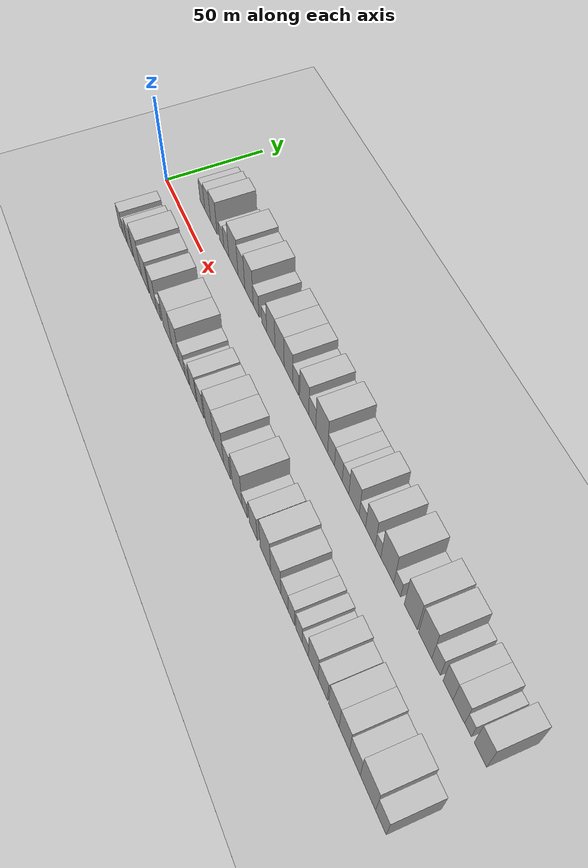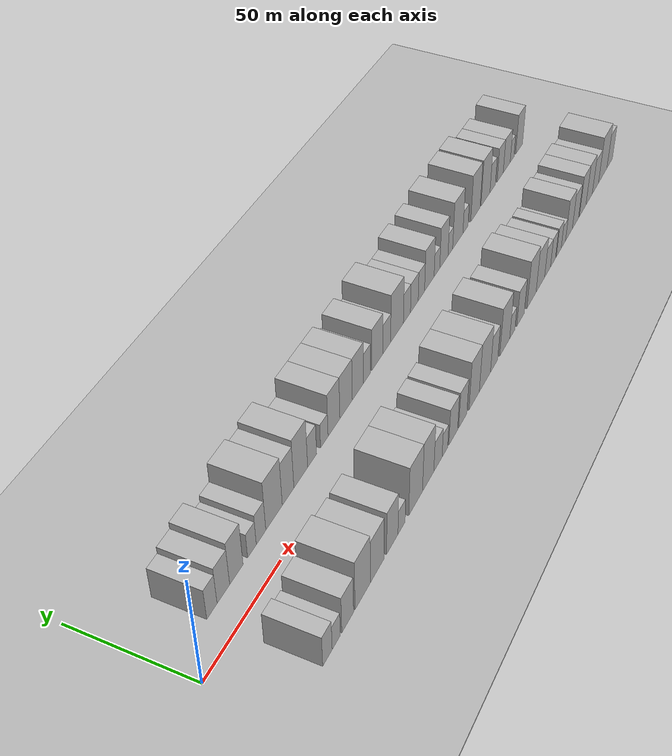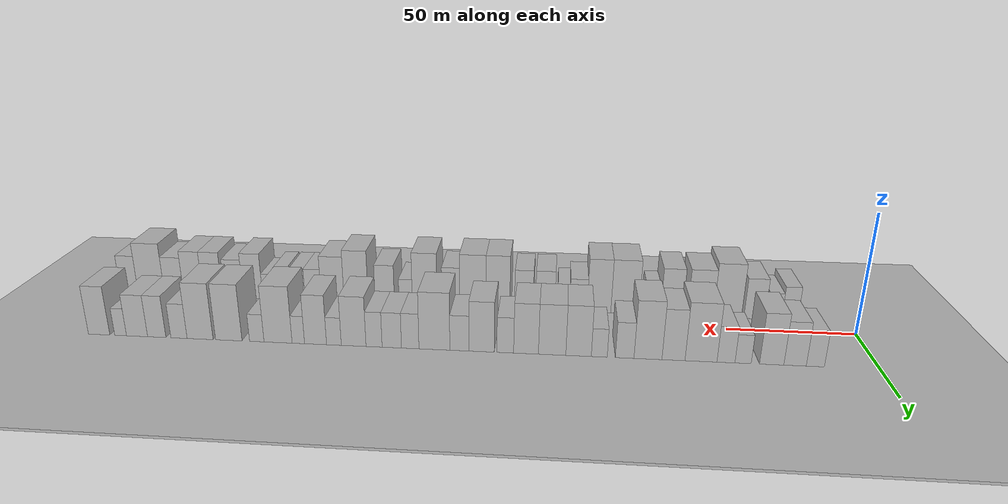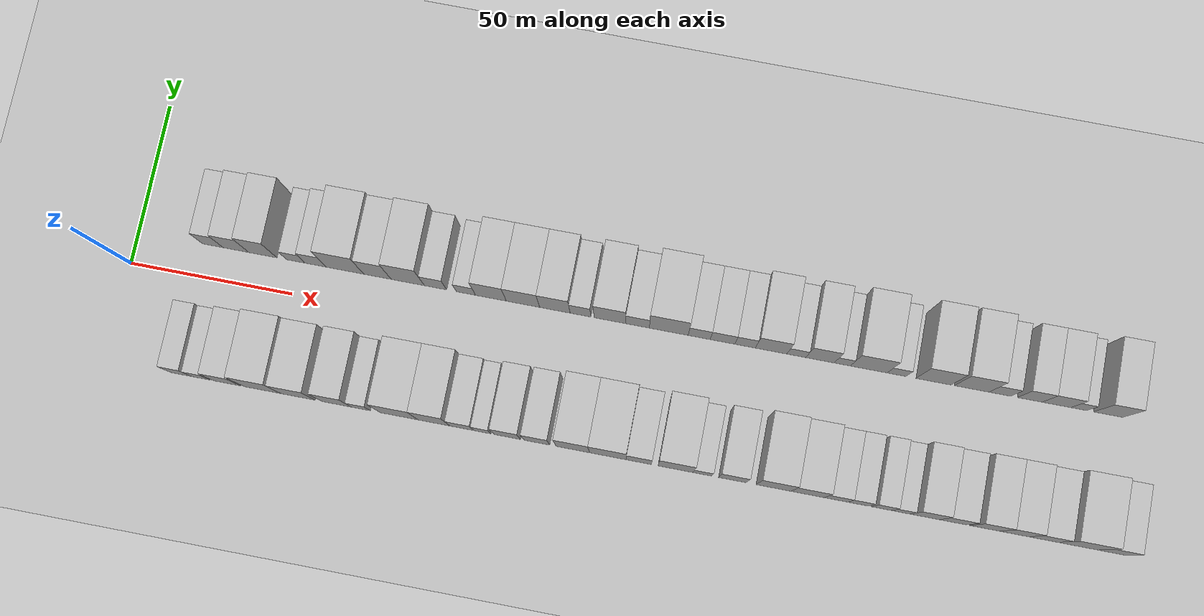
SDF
<?xml version="1.0" encoding="utf-8"?>

<sdf version="1.6">

   <world name="default">

      <gui fullscreen="0">

         <camera name="user_camera">

            <pose>-15 0 4.57585 0 0 0</pose>

            <view_controller>orbit</view_controller>

         </camera>

      </gui>

      <scene>

         <sky>

           <clouds>

             <speed>12</speed>

           </clouds>

         </sky>

         <ambient>0.4 0.4 0.4 1</ambient>

         <background>0.7 0.7 0.7 1</background>

         <shadows>1</shadows>

      </scene>

      <gravity>0 0 -9.8066</gravity>

      <magnetic_field>6e-06 2.3e-05 -4.2e-05</magnetic_field>

      <physics default="0" name="default_physics" type="ode">

         <ode>

            <solver>

               <type>quick</type>

               <iters>10</iters>

               <sor>1.0</sor>

               <use_dynamic_moi_rescaling>0</use_dynamic_moi_rescaling>

            </solver>

            <constraints>

               <cfm>0</cfm>

               <erp>0.2</erp>

               <contact_max_correcting_vel>100</contact_max_correcting_vel>

               <contact_surface_layer>0.001</contact_surface_layer>

            </constraints>

         </ode>

         <max_step_size>0.004</max_step_size>

         <real_time_factor>1</real_time_factor>

         <real_time_update_rate>250</real_time_update_rate>

      </physics>

      <light name="sun" type="directional">

         <cast_shadows>1</cast_shadows>

         <pose>0 0 10 0 0 0</pose>

         <diffuse>0.8 0.8 0.8 1</diffuse>

         <specular>0.2 0.2 0.2 1</specular>

         <attenuation>

            <range>1000</range>

            <constant>0.9</constant>

            <linear>0.01</linear>

            <quadratic>0.001</quadratic>

         </attenuation>

         <direction>-0.5 0.1 -0.9</direction>

      </light>

      <include>

         <name>ground_plane_1</name>

         <uri>model://HANNAS_ground_plane</uri>

         <pose>0 0 0  0 0 0</pose>

      </include>

      <include>

         <name>ground_plane_2</name>

         <uri>model://HANNAS_ground_plane</uri>

         <pose>100 0 0  0 0 0</pose>

      </include>

      <model name="building_1">

         <static>1</static>

         <pose frame="">23.2185 20.0000 0 0.000000 0.000000 1.570796</pose>

         <link name="link">

            <pose frame="">0 0 7.50 0 0 0</pose>

            <collision name="collision">

               <geometry>

                  <box>

                     <size>20.0000 6.4370 15.0000</size>

                  </box>

               </geometry>

               <max_contacts>10</max_contacts>

               <surface>

                  <contact>

                     <ode/>

                  </contact>

                  <bounce/>

                  <friction>

                     <torsional>

                        <ode/>

                     </torsional>

                     <ode/>

                  </friction>

               </surface>

            </collision>

            <visual name="visual">

               <cast_shadows>0</cast_shadows>

               <geometry>

                  <box>

                     <size>20.0000 6.4370 15.0000</size>

                  </box>

               </geometry>

               <material>

                  <script>

                     <uri>model://HANNAS_wall/materials/scripts</uri>

                     <uri>model://HANNAS_wall/materials/textures</uri>

                     <name>vrc/HANNAS_wall</name>

                  </script>

               </material>

            </visual>

            <self_collide>0</self_collide>

            <enable_wind>0</enable_wind>

            <kinematic>0</kinematic>

         </link>

      </model>

      <model name="building_2">

         <static>1</static>

         <pose frame="">30.4267 20.0000 0 0.000000 0.000000 1.570796</pose>

         <link name="link">

            <pose frame="">0 0 9.00 0 0 0</pose>

            <collision name="collision">

               <geometry>

                  <box>

                     <size>20.0000 7.9793 18.0000</size>

                  </box>

               </geometry>

               <max_contacts>10</max_contacts>

               <surface>

                  <contact>

                     <ode/>

                  </contact>

                  <bounce/>

                  <friction>

                     <torsional>

                        <ode/>

                     </torsional>

                     <ode/>

                  </friction>

               </surface>

            </collision>

            <visual name="visual">

               <cast_shadows>0</cast_shadows>

               <geometry>

                  <box>

                     <size>20.0000 7.9793 18.0000</size>

                  </box>

               </geometry>

               <material>

                  <script>

                     <uri>model://HANNAS_wall/materials/scripts</uri>

                     <uri>model://HANNAS_wall/materials/textures</uri>

                     <name>vrc/HANNAS_wall</name>

                  </script>

               </material>

            </visual>

            <self_collide>0</self_collide>

            <enable_wind>0</enable_wind>

            <kinematic>0</kinematic>

         </link>

      </model>

      <model name="building_3">

         <static>1</static>

         <pose frame="">38.7653 20.0000 0 0.000000 0.000000 1.570796</pose>

         <link name="link">

            <pose frame="">0 0 10.50 0 0 0</pose>

            <collision name="collision">

               <geometry>

                  <box>

                     <size>20.0000 8.6980 21.0000</size>

                  </box>

               </geometry>

               <max_contacts>10</max_contacts>

               <surface>

                  <contact>

                     <ode/>

                  </contact>

                  <bounce/>

                  <friction>

                     <torsional>

                        <ode/>

                     </torsional>

                     <ode/>

                  </friction>

               </surface>

            </collision>

            <visual name="visual">

               <cast_shadows>0</cast_shadows>

               <geometry>

                  <box>

                     <size>20.0000 8.6980 21.0000</size>

                  </box>

               </geometry>

               <material>

                  <script>

                     <uri>model://HANNAS_wall/materials/scripts</uri>

                     <uri>model://HANNAS_wall/materials/textures</uri>

                     <name>vrc/HANNAS_wall</name>

                  </script>

               </material>

            </visual>

            <self_collide>0</self_collide>

            <enable_wind>0</enable_wind>

            <kinematic>0</kinematic>

         </link>

      </model>

      <model name="building_4">

         <static>1</static>

         <pose frame="">49.0297 20.0000 0 0.000000 0.000000 1.570796</pose>

         <link name="link">

            <pose frame="">0 0 6.00 0 0 0</pose>

            <collision name="collision">

               <geometry>

                  <box>

                     <size>20.0000 5.8307 12.0000</size>

                  </box>

               </geometry>

               <max_contacts>10</max_contacts>

               <surface>

                  <contact>

                     <ode/>

                  </contact>

                  <bounce/>

                  <friction>

                     <torsional>

                        <ode/>

                     </torsional>

                     <ode/>

                  </friction>

               </surface>

            </collision>

            <visual name="visual">

               <cast_shadows>0</cast_shadows>

               <geometry>

                  <box>

                     <size>20.0000 5.8307 12.0000</size>

                  </box>

               </geometry>

               <material>

                  <script>

                     <uri>model://HANNAS_wall/materials/scripts</uri>

                     <uri>model://HANNAS_wall/materials/textures</uri>

                     <name>vrc/HANNAS_wall</name>

                  </script>

               </material>

            </visual>

            <self_collide>0</self_collide>

            <enable_wind>0</enable_wind>

            <kinematic>0</kinematic>

         </link>

      </model>

      <model name="building_5">

         <static>1</static>

         <pose frame="">55.2006 20.0000 0 0.000000 0.000000 1.570796</pose>

         <link name="link">

            <pose frame="">0 0 7.50 0 0 0</pose>

            <collision name="collision">

               <geometry>

                  <box>

                     <size>20.0000 6.5111 15.0000</size>

                  </box>

               </geometry>

               <max_contacts>10</max_contacts>

               <surface>

                  <contact>

                     <ode/>

                  </contact>

                  <bounce/>

                  <friction>

                     <torsional>

                        <ode/>

                     </torsional>

                     <ode/>

                  </friction>

               </surface>

            </collision>

            <visual name="visual">

               <cast_shadows>0</cast_shadows>

               <geometry>

                  <box>

                     <size>20.0000 6.5111 15.0000</size>

                  </box>

               </geometry>

               <material>

                  <script>

                     <uri>model://HANNAS_wall/materials/scripts</uri>

                     <uri>model://HANNAS_wall/materials/textures</uri>

                     <name>vrc/HANNAS_wall</name>

                  </script>

               </material>

            </visual>

            <self_collide>0</self_collide>

            <enable_wind>0</enable_wind>

            <kinematic>0</kinematic>

         </link>

      </model>

      <model name="building_6">

         <static>1</static>

         <pose frame="">64.2493 20.0000 0 0.000000 0.000000 1.570796</pose>

         <link name="link">

            <pose frame="">0 0 12.00 0 0 0</pose>

            <collision name="collision">

               <geometry>

                  <box>

                     <size>20.0000 11.5862 24.0000</size>

                  </box>

               </geometry>

               <max_contacts>10</max_contacts>

               <surface>

                  <contact>

                     <ode/>

                  </contact>

                  <bounce/>

                  <friction>

                     <torsional>

                        <ode/>

                     </torsional>

                     <ode/>

                  </friction>

               </surface>

            </collision>

            <visual name="visual">

               <cast_shadows>0</cast_shadows>

               <geometry>

                  <box>

                     <size>20.0000 11.5862 24.0000</size>

                  </box>

               </geometry>

               <material>

                  <script>

                     <uri>model://HANNAS_wall/materials/scripts</uri>

                     <uri>model://HANNAS_wall/materials/textures</uri>

                     <name>vrc/HANNAS_wall</name>

                  </script>

               </material>

            </visual>

            <self_collide>0</self_collide>

            <enable_wind>0</enable_wind>

            <kinematic>0</kinematic>

         </link>

      </model>

      <model name="building_7">

         <static>1</static>

         <pose frame="">74.2523 20.0000 0 0.000000 0.000000 1.570796</pose>

         <link name="link">

            <pose frame="">0 0 10.50 0 0 0</pose>

            <collision name="collision">

               <geometry>

                  <box>

                     <size>20.0000 8.4197 21.0000</size>

                  </box>

               </geometry>

               <max_contacts>10</max_contacts>

               <surface>

                  <contact>

                     <ode/>

                  </contact>

                  <bounce/>

                  <friction>

                     <torsional>

                        <ode/>

                     </torsional>

                     <ode/>

                  </friction>

               </surface>

            </collision>

            <visual name="visual">

               <cast_shadows>0</cast_shadows>

               <geometry>

                  <box>

                     <size>20.0000 8.4197 21.0000</size>

                  </box>

               </geometry>

               <material>

                  <script>

                     <uri>model://HANNAS_wall/materials/scripts</uri>

                     <uri>model://HANNAS_wall/materials/textures</uri>

                     <name>vrc/HANNAS_wall</name>

                  </script>

               </material>

            </visual>

            <self_collide>0</self_collide>

            <enable_wind>0</enable_wind>

            <kinematic>0</kinematic>

         </link>

      </model>

      <model name="building_8">

         <static>1</static>

         <pose frame="">83.5853 20.0000 0 0.000000 0.000000 1.570796</pose>

         <link name="link">

            <pose frame="">0 0 12.00 0 0 0</pose>

            <collision name="collision">

               <geometry>

                  <box>

                     <size>20.0000 10.2463 24.0000</size>

                  </box>

               </geometry>

               <max_contacts>10</max_contacts>

               <surface>

                  <contact>

                     <ode/>

                  </contact>

                  <bounce/>

                  <friction>

                     <torsional>

                        <ode/>

                     </torsional>

                     <ode/>

                  </friction>

               </surface>

            </collision>

            <visual name="visual">

               <cast_shadows>0</cast_shadows>

               <geometry>

                  <box>

                     <size>20.0000 10.2463 24.0000</size>

                  </box>

               </geometry>

               <material>

                  <script>

                     <uri>model://HANNAS_wall/materials/scripts</uri>

                     <uri>model://HANNAS_wall/materials/textures</uri>

                     <name>vrc/HANNAS_wall</name>

                  </script>

               </material>

            </visual>

            <self_collide>0</self_collide>

            <enable_wind>0</enable_wind>

            <kinematic>0</kinematic>

         </link>

      </model>

      <model name="building_9">

         <static>1</static>

         <pose frame="">92.1335 20.0000 0 0.000000 0.000000 1.570796</pose>

         <link name="link">

            <pose frame="">0 0 7.50 0 0 0</pose>

            <collision name="collision">

               <geometry>

                  <box>

                     <size>20.0000 6.8501 15.0000</size>

                  </box>

               </geometry>

               <max_contacts>10</max_contacts>

               <surface>

                  <contact>

                     <ode/>

                  </contact>

                  <bounce/>

                  <friction>

                     <torsional>

                        <ode/>

                     </torsional>

                     <ode/>

                  </friction>

               </surface>

            </collision>

            <visual name="visual">

               <cast_shadows>0</cast_shadows>

               <geometry>

                  <box>

                     <size>20.0000 6.8501 15.0000</size>

                  </box>

               </geometry>

               <material>

                  <script>

                     <uri>model://HANNAS_wall/materials/scripts</uri>

                     <uri>model://HANNAS_wall/materials/textures</uri>

                     <name>vrc/HANNAS_wall</name>

                  </script>

               </material>

            </visual>

            <self_collide>0</self_collide>

            <enable_wind>0</enable_wind>

            <kinematic>0</kinematic>

         </link>

      </model>

      <model name="building_10">

         <static>1</static>

         <pose frame="">101.5094 20.0000 0 0.000000 0.000000 1.570796</pose>

         <link name="link">

            <pose frame="">0 0 6.00 0 0 0</pose>

            <collision name="collision">

               <geometry>

                  <box>

                     <size>20.0000 5.9017 12.0000</size>

                  </box>

               </geometry>

               <max_contacts>10</max_contacts>

               <surface>

                  <contact>

                     <ode/>

                  </contact>

                  <bounce/>

                  <friction>

                     <torsional>

                        <ode/>

                     </torsional>

                     <ode/>

                  </friction>

               </surface>

            </collision>

            <visual name="visual">

               <cast_shadows>0</cast_shadows>

               <geometry>

                  <box>

                     <size>20.0000 5.9017 12.0000</size>

                  </box>

               </geometry>

               <material>

                  <script>

                     <uri>model://HANNAS_wall/materials/scripts</uri>

                     <uri>model://HANNAS_wall/materials/textures</uri>

                     <name>vrc/HANNAS_wall</name>

                  </script>

               </material>

            </visual>

            <self_collide>0</self_collide>

            <enable_wind>0</enable_wind>

            <kinematic>0</kinematic>

         </link>

      </model>

      <model name="building_11">

         <static>1</static>

         <pose frame="">109.1978 20.0000 0 0.000000 0.000000 1.570796</pose>

         <link name="link">

            <pose frame="">0 0 10.50 0 0 0</pose>

            <collision name="collision">

               <geometry>

                  <box>

                     <size>20.0000 9.4750 21.0000</size>

                  </box>

               </geometry>

               <max_contacts>10</max_contacts>

               <surface>

                  <contact>

                     <ode/>

                  </contact>

                  <bounce/>

                  <friction>

                     <torsional>

                        <ode/>

                     </torsional>

                     <ode/>

                  </friction>

               </surface>

            </collision>

            <visual name="visual">

               <cast_shadows>0</cast_shadows>

               <geometry>

                  <box>

                     <size>20.0000 9.4750 21.0000</size>

                  </box>

               </geometry>

               <material>

                  <script>

                     <uri>model://HANNAS_wall/materials/scripts</uri>

                     <uri>model://HANNAS_wall/materials/textures</uri>

                     <name>vrc/HANNAS_wall</name>

                  </script>

               </material>

            </visual>

            <self_collide>0</self_collide>

            <enable_wind>0</enable_wind>

            <kinematic>0</kinematic>

         </link>

      </model>

      <model name="building_12">

         <static>1</static>

         <pose frame="">119.0571 20.0000 0 0.000000 0.000000 1.570796</pose>

         <link name="link">

            <pose frame="">0 0 10.50 0 0 0</pose>

            <collision name="collision">

               <geometry>

                  <box>

                     <size>20.0000 10.2438 21.0000</size>

                  </box>

               </geometry>

               <max_contacts>10</max_contacts>

               <surface>

                  <contact>

                     <ode/>

                  </contact>

                  <bounce/>

                  <friction>

                     <torsional>

                        <ode/>

                     </torsional>

                     <ode/>

                  </friction>

               </surface>

            </collision>

            <visual name="visual">

               <cast_shadows>0</cast_shadows>

               <geometry>

                  <box>

                     <size>20.0000 10.2438 21.0000</size>

                  </box>

               </geometry>

               <material>

                  <script>

                     <uri>model://HANNAS_wall/materials/scripts</uri>

                     <uri>model://HANNAS_wall/materials/textures</uri>

                     <name>vrc/HANNAS_wall</name>

                  </script>

               </material>

            </visual>

            <self_collide>0</self_collide>

            <enable_wind>0</enable_wind>

            <kinematic>0</kinematic>

         </link>

      </model>

      <model name="building_13">

         <static>1</static>

         <pose frame="">128.8372 20.0000 0 0.000000 0.000000 1.570796</pose>

         <link name="link">

            <pose frame="">0 0 10.50 0 0 0</pose>

            <collision name="collision">

               <geometry>

                  <box>

                     <size>20.0000 9.3164 21.0000</size>

                  </box>

               </geometry>

               <max_contacts>10</max_contacts>

               <surface>

                  <contact>

                     <ode/>

                  </contact>

                  <bounce/>

                  <friction>

                     <torsional>

                        <ode/>

                     </torsional>

                     <ode/>

                  </friction>

               </surface>

            </collision>

            <visual name="visual">

               <cast_shadows>0</cast_shadows>

               <geometry>

                  <box>

                     <size>20.0000 9.3164 21.0000</size>

                  </box>

               </geometry>

               <material>

                  <script>

                     <uri>model://HANNAS_wall/materials/scripts</uri>

                     <uri>model://HANNAS_wall/materials/textures</uri>

                     <name>vrc/HANNAS_wall</name>

                  </script>

               </material>

            </visual>

            <self_collide>0</self_collide>

            <enable_wind>0</enable_wind>

            <kinematic>0</kinematic>

         </link>

      </model>

      <model name="building_14">

         <static>1</static>

         <pose frame="">136.6634 20.0000 0 0.000000 0.000000 1.570796</pose>

         <link name="link">

            <pose frame="">0 0 7.50 0 0 0</pose>

            <collision name="collision">

               <geometry>

                  <box>

                     <size>20.0000 6.3360 15.0000</size>

                  </box>

               </geometry>

               <max_contacts>10</max_contacts>

               <surface>

                  <contact>

                     <ode/>

                  </contact>

                  <bounce/>

                  <friction>

                     <torsional>

                        <ode/>

                     </torsional>

                     <ode/>

                  </friction>

               </surface>

            </collision>

            <visual name="visual">

               <cast_shadows>0</cast_shadows>

               <geometry>

                  <box>

                     <size>20.0000 6.3360 15.0000</size>

                  </box>

               </geometry>

               <material>

                  <script>

                     <uri>model://HANNAS_wall/materials/scripts</uri>

                     <uri>model://HANNAS_wall/materials/textures</uri>

                     <name>vrc/HANNAS_wall</name>

                  </script>

               </material>

            </visual>

            <self_collide>0</self_collide>

            <enable_wind>0</enable_wind>

            <kinematic>0</kinematic>

         </link>

      </model>

      <model name="building_15">

         <static>1</static>

         <pose frame="">145.6636 20.0000 0 0.000000 0.000000 1.570796</pose>

         <link name="link">

            <pose frame="">0 0 10.50 0 0 0</pose>

            <collision name="collision">

               <geometry>

                  <box>

                     <size>20.0000 9.6642 21.0000</size>

                  </box>

               </geometry>

               <max_contacts>10</max_contacts>

               <surface>

                  <contact>

                     <ode/>

                  </contact>

                  <bounce/>

                  <friction>

                     <torsional>

                        <ode/>

                     </torsional>

                     <ode/>

                  </friction>

               </surface>

            </collision>

            <visual name="visual">

               <cast_shadows>0</cast_shadows>

               <geometry>

                  <box>

                     <size>20.0000 9.6642 21.0000</size>

                  </box>

               </geometry>

               <material>

                  <script>

                     <uri>model://HANNAS_wall/materials/scripts</uri>

                     <uri>model://HANNAS_wall/materials/textures</uri>

                     <name>vrc/HANNAS_wall</name>

                  </script>

               </material>

            </visual>

            <self_collide>0</self_collide>

            <enable_wind>0</enable_wind>

            <kinematic>0</kinematic>

         </link>

      </model>

      <model name="building_16">

         <static>1</static>

         <pose frame="">154.0857 20.0000 0 0.000000 0.000000 1.570796</pose>

         <link name="link">

            <pose frame="">0 0 7.50 0 0 0</pose>

            <collision name="collision">

               <geometry>

                  <box>

                     <size>20.0000 7.1800 15.0000</size>

                  </box>

               </geometry>

               <max_contacts>10</max_contacts>

               <surface>

                  <contact>

                     <ode/>

                  </contact>

                  <bounce/>

                  <friction>

                     <torsional>

                        <ode/>

                     </torsional>

                     <ode/>

                  </friction>

               </surface>

            </collision>

            <visual name="visual">

               <cast_shadows>0</cast_shadows>

               <geometry>

                  <box>

                     <size>20.0000 7.1800 15.0000</size>

                  </box>

               </geometry>

               <material>

                  <script>

                     <uri>model://HANNAS_wall/materials/scripts</uri>

                     <uri>model://HANNAS_wall/materials/textures</uri>

                     <name>vrc/HANNAS_wall</name>

                  </script>

               </material>

            </visual>

            <self_collide>0</self_collide>

            <enable_wind>0</enable_wind>

            <kinematic>0</kinematic>

         </link>

      </model>

      <model name="building_17">

         <static>1</static>

         <pose frame="">163.5873 20.0000 0 0.000000 0.000000 1.570796</pose>

         <link name="link">

            <pose frame="">0 0 12.00 0 0 0</pose>

            <collision name="collision">

               <geometry>

                  <box>

                     <size>20.0000 11.8232 24.0000</size>

                  </box>

               </geometry>

               <max_contacts>10</max_contacts>

               <surface>

                  <contact>

                     <ode/>

                  </contact>

                  <bounce/>

                  <friction>

                     <torsional>

                        <ode/>

                     </torsional>

                     <ode/>

                  </friction>

               </surface>

            </collision>

            <visual name="visual">

               <cast_shadows>0</cast_shadows>

               <geometry>

                  <box>

                     <size>20.0000 11.8232 24.0000</size>

                  </box>

               </geometry>

               <material>

                  <script>

                     <uri>model://HANNAS_wall/materials/scripts</uri>

                     <uri>model://HANNAS_wall/materials/textures</uri>

                     <name>vrc/HANNAS_wall</name>

                  </script>

               </material>

            </visual>

            <self_collide>0</self_collide>

            <enable_wind>0</enable_wind>

            <kinematic>0</kinematic>

         </link>

      </model>

      <model name="building_18">

         <static>1</static>

         <pose frame="">172.8582 20.0000 0 0.000000 0.000000 1.570796</pose>

         <link name="link">

            <pose frame="">0 0 7.50 0 0 0</pose>

            <collision name="collision">

               <geometry>

                  <box>

                     <size>20.0000 6.7187 15.0000</size>

                  </box>

               </geometry>

               <max_contacts>10</max_contacts>

               <surface>

                  <contact>

                     <ode/>

                  </contact>

                  <bounce/>

                  <friction>

                     <torsional>

                        <ode/>

                     </torsional>

                     <ode/>

                  </friction>

               </surface>

            </collision>

            <visual name="visual">

               <cast_shadows>0</cast_shadows>

               <geometry>

                  <box>

                     <size>20.0000 6.7187 15.0000</size>

                  </box>

               </geometry>

               <material>

                  <script>

                     <uri>model://HANNAS_wall/materials/scripts</uri>

                     <uri>model://HANNAS_wall/materials/textures</uri>

                     <name>vrc/HANNAS_wall</name>

                  </script>

               </material>

            </visual>

            <self_collide>0</self_collide>

            <enable_wind>0</enable_wind>

            <kinematic>0</kinematic>

         </link>

      </model>

      <model name="building_19">

         <static>1</static>

         <pose frame="">179.9510 20.0000 0 0.000000 0.000000 1.570796</pose>

         <link name="link">

            <pose frame="">0 0 7.50 0 0 0</pose>

            <collision name="collision">

               <geometry>

                  <box>

                     <size>20.0000 7.4668 15.0000</size>

                  </box>

               </geometry>

               <max_contacts>10</max_contacts>

               <surface>

                  <contact>

                     <ode/>

                  </contact>

                  <bounce/>

                  <friction>

                     <torsional>

                        <ode/>

                     </torsional>

                     <ode/>

                  </friction>

               </surface>

            </collision>

            <visual name="visual">

               <cast_shadows>0</cast_shadows>

               <geometry>

                  <box>

                     <size>20.0000 7.4668 15.0000</size>

                  </box>

               </geometry>

               <material>

                  <script>

                     <uri>model://HANNAS_wall/materials/scripts</uri>

                     <uri>model://HANNAS_wall/materials/textures</uri>

                     <name>vrc/HANNAS_wall</name>

                  </script>

               </material>

            </visual>

            <self_collide>0</self_collide>

            <enable_wind>0</enable_wind>

            <kinematic>0</kinematic>

         </link>

      </model>

      <model name="building_20">

         <static>1</static>

         <pose frame="">186.8059 20.0000 0 0.000000 0.000000 1.570796</pose>

         <link name="link">

            <pose frame="">0 0 7.50 0 0 0</pose>

            <collision name="collision">

               <geometry>

                  <box>

                     <size>20.0000 6.2430 15.0000</size>

                  </box>

               </geometry>

               <max_contacts>10</max_contacts>

               <surface>

                  <contact>

                     <ode/>

                  </contact>

                  <bounce/>

                  <friction>

                     <torsional>

                        <ode/>

                     </torsional>

                     <ode/>

                  </friction>

               </surface>

            </collision>

            <visual name="visual">

               <cast_shadows>0</cast_shadows>

               <geometry>

                  <box>

                     <size>20.0000 6.2430 15.0000</size>

                  </box>

               </geometry>

               <material>

                  <script>

                     <uri>model://HANNAS_wall/materials/scripts</uri>

                     <uri>model://HANNAS_wall/materials/textures</uri>

                     <name>vrc/HANNAS_wall</name>

                  </script>

               </material>

            </visual>

            <self_collide>0</self_collide>

            <enable_wind>0</enable_wind>

            <kinematic>0</kinematic>

         </link>

      </model>

      <model name="building_21">

         <static>1</static>

         <pose frame="">194.7337 20.0000 0 0.000000 0.000000 1.570796</pose>

         <link name="link">

            <pose frame="">0 0 10.50 0 0 0</pose>

            <collision name="collision">

               <geometry>

                  <box>

                     <size>20.0000 9.6127 21.0000</size>

                  </box>

               </geometry>

               <max_contacts>10</max_contacts>

               <surface>

                  <contact>

                     <ode/>

                  </contact>

                  <bounce/>

                  <friction>

                     <torsional>

                        <ode/>

                     </torsional>

                     <ode/>

                  </friction>

               </surface>

            </collision>

            <visual name="visual">

               <cast_shadows>0</cast_shadows>

               <geometry>

                  <box>

                     <size>20.0000 9.6127 21.0000</size>

                  </box>

               </geometry>

               <material>

                  <script>

                     <uri>model://HANNAS_wall/materials/scripts</uri>

                     <uri>model://HANNAS_wall/materials/textures</uri>

                     <name>vrc/HANNAS_wall</name>

                  </script>

               </material>

            </visual>

            <self_collide>0</self_collide>

            <enable_wind>0</enable_wind>

            <kinematic>0</kinematic>

         </link>

      </model>

      <model name="building_22">

         <static>1</static>

         <pose frame="">202.4195 20.0000 0 0.000000 0.000000 1.570796</pose>

         <link name="link">

            <pose frame="">0 0 6.00 0 0 0</pose>

            <collision name="collision">

               <geometry>

                  <box>

                     <size>20.0000 5.7590 12.0000</size>

                  </box>

               </geometry>

               <max_contacts>10</max_contacts>

               <surface>

                  <contact>

                     <ode/>

                  </contact>

                  <bounce/>

                  <friction>

                     <torsional>

                        <ode/>

                     </torsional>

                     <ode/>

                  </friction>

               </surface>

            </collision>

            <visual name="visual">

               <cast_shadows>0</cast_shadows>

               <geometry>

                  <box>

                     <size>20.0000 5.7590 12.0000</size>

                  </box>

               </geometry>

               <material>

                  <script>

                     <uri>model://HANNAS_wall/materials/scripts</uri>

                     <uri>model://HANNAS_wall/materials/textures</uri>

                     <name>vrc/HANNAS_wall</name>

                  </script>

               </material>

            </visual>

            <self_collide>0</self_collide>

            <enable_wind>0</enable_wind>

            <kinematic>0</kinematic>

         </link>

      </model>

      <model name="building_23">

         <static>1</static>

         <pose frame="">209.6194 20.0000 0 0.000000 0.000000 1.570796</pose>

         <link name="link">

            <pose frame="">0 0 10.50 0 0 0</pose>

            <collision name="collision">

               <geometry>

                  <box>

                     <size>20.0000 8.6408 21.0000</size>

                  </box>

               </geometry>

               <max_contacts>10</max_contacts>

               <surface>

                  <contact>

                     <ode/>

                  </contact>

                  <bounce/>

                  <friction>

                     <torsional>

                        <ode/>

                     </torsional>

                     <ode/>

                  </friction>

               </surface>

            </collision>

            <visual name="visual">

               <cast_shadows>0</cast_shadows>

               <geometry>

                  <box>

                     <size>20.0000 8.6408 21.0000</size>

                  </box>

               </geometry>

               <material>

                  <script>

                     <uri>model://HANNAS_wall/materials/scripts</uri>

                     <uri>model://HANNAS_wall/materials/textures</uri>

                     <name>vrc/HANNAS_wall</name>

                  </script>

               </material>

            </visual>

            <self_collide>0</self_collide>

            <enable_wind>0</enable_wind>

            <kinematic>0</kinematic>

         </link>

      </model>

      <model name="building_24">

         <static>1</static>

         <pose frame="">216.3838 20.0000 0 0.000000 0.000000 1.570796</pose>

         <link name="link">

            <pose frame="">0 0 6.00 0 0 0</pose>

            <collision name="collision">

               <geometry>

                  <box>

                     <size>20.0000 4.8879 12.0000</size>

                  </box>

               </geometry>

               <max_contacts>10</max_contacts>

               <surface>

                  <contact>

                     <ode/>

                  </contact>

                  <bounce/>

                  <friction>

                     <torsional>

                        <ode/>

                     </torsional>

                     <ode/>

                  </friction>

               </surface>

            </collision>

            <visual name="visual">

               <cast_shadows>0</cast_shadows>

               <geometry>

                  <box>

                     <size>20.0000 4.8879 12.0000</size>

                  </box>

               </geometry>

               <material>

                  <script>

                     <uri>model://HANNAS_wall/materials/scripts</uri>

                     <uri>model://HANNAS_wall/materials/textures</uri>

                     <name>vrc/HANNAS_wall</name>

                  </script>

               </material>

            </visual>

            <self_collide>0</self_collide>

            <enable_wind>0</enable_wind>

            <kinematic>0</kinematic>

         </link>

      </model>

      <model name="building_25">

         <static>1</static>

         <pose frame="">224.3816 20.0000 0 0.000000 0.000000 1.570796</pose>

         <link name="link">

            <pose frame="">0 0 12.00 0 0 0</pose>

            <collision name="collision">

               <geometry>

                  <box>

                     <size>20.0000 11.1077 24.0000</size>

                  </box>

               </geometry>

               <max_contacts>10</max_contacts>

               <surface>

                  <contact>

                     <ode/>

                  </contact>

                  <bounce/>

                  <friction>

                     <torsional>

                        <ode/>

                     </torsional>

                     <ode/>

                  </friction>

               </surface>

            </collision>

            <visual name="visual">

               <cast_shadows>0</cast_shadows>

               <geometry>

                  <box>

                     <size>20.0000 11.1077 24.0000</size>

                  </box>

               </geometry>

               <material>

                  <script>

                     <uri>model://HANNAS_wall/materials/scripts</uri>

                     <uri>model://HANNAS_wall/materials/textures</uri>

                     <name>vrc/HANNAS_wall</name>

                  </script>

               </material>

            </visual>

            <self_collide>0</self_collide>

            <enable_wind>0</enable_wind>

            <kinematic>0</kinematic>

         </link>

      </model>

      <model name="building_26">

         <static>1</static>

         <pose frame="">232.8020 20.0000 0 0.000000 0.000000 1.570796</pose>

         <link name="link">

            <pose frame="">0 0 6.00 0 0 0</pose>

            <collision name="collision">

               <geometry>

                  <box>

                     <size>20.0000 5.7331 12.0000</size>

                  </box>

               </geometry>

               <max_contacts>10</max_contacts>

               <surface>

                  <contact>

                     <ode/>

                  </contact>

                  <bounce/>

                  <friction>

                     <torsional>

                        <ode/>

                     </torsional>

                     <ode/>

                  </friction>

               </surface>

            </collision>

            <visual name="visual">

               <cast_shadows>0</cast_shadows>

               <geometry>

                  <box>

                     <size>20.0000 5.7331 12.0000</size>

                  </box>

               </geometry>

               <material>

                  <script>

                     <uri>model://HANNAS_wall/materials/scripts</uri>

                     <uri>model://HANNAS_wall/materials/textures</uri>

                     <name>vrc/HANNAS_wall</name>

                  </script>

               </material>

            </visual>

            <self_collide>0</self_collide>

            <enable_wind>0</enable_wind>

            <kinematic>0</kinematic>

         </link>

      </model>

      <model name="building_27">

         <static>1</static>

         <pose frame="">243.9484 20.0000 0 0.000000 0.000000 1.570796</pose>

         <link name="link">

            <pose frame="">0 0 12.00 0 0 0</pose>

            <collision name="collision">

               <geometry>

                  <box>

                     <size>20.0000 10.5597 24.0000</size>

                  </box>

               </geometry>

               <max_contacts>10</max_contacts>

               <surface>

                  <contact>

                     <ode/>

                  </contact>

                  <bounce/>

                  <friction>

                     <torsional>

                        <ode/>

                     </torsional>

                     <ode/>

                  </friction>

               </surface>

            </collision>

            <visual name="visual">

               <cast_shadows>0</cast_shadows>

               <geometry>

                  <box>

                     <size>20.0000 10.5597 24.0000</size>

                  </box>

               </geometry>

               <material>

                  <script>

                     <uri>model://HANNAS_wall/materials/scripts</uri>

                     <uri>model://HANNAS_wall/materials/textures</uri>

                     <name>vrc/HANNAS_wall</name>

                  </script>

               </material>

            </visual>

            <self_collide>0</self_collide>

            <enable_wind>0</enable_wind>

            <kinematic>0</kinematic>

         </link>

      </model>

      <model name="building_28">

         <static>1</static>

         <pose frame="">255.4477 20.0000 0 0.000000 0.000000 1.570796</pose>

         <link name="link">

            <pose frame="">0 0 12.00 0 0 0</pose>

            <collision name="collision">

               <geometry>

                  <box>

                     <size>20.0000 10.4390 24.0000</size>

                  </box>

               </geometry>

               <max_contacts>10</max_contacts>

               <surface>

                  <contact>

                     <ode/>

                  </contact>

                  <bounce/>

                  <friction>

                     <torsional>

                        <ode/>

                     </torsional>

                     <ode/>

                  </friction>

               </surface>

            </collision>

            <visual name="visual">

               <cast_shadows>0</cast_shadows>

               <geometry>

                  <box>

                     <size>20.0000 10.4390 24.0000</size>

                  </box>

               </geometry>

               <material>

                  <script>

                     <uri>model://HANNAS_wall/materials/scripts</uri>

                     <uri>model://HANNAS_wall/materials/textures</uri>

                     <name>vrc/HANNAS_wall</name>

                  </script>

               </material>

            </visual>

            <self_collide>0</self_collide>

            <enable_wind>0</enable_wind>

            <kinematic>0</kinematic>

         </link>

      </model>

      <model name="building_29">

         <static>1</static>

         <pose frame="">263.9485 20.0000 0 0.000000 0.000000 1.570796</pose>

         <link name="link">

            <pose frame="">0 0 7.50 0 0 0</pose>

            <collision name="collision">

               <geometry>

                  <box>

                     <size>20.0000 6.5625 15.0000</size>

                  </box>

               </geometry>

               <max_contacts>10</max_contacts>

               <surface>

                  <contact>

                     <ode/>

                  </contact>

                  <bounce/>

                  <friction>

                     <torsional>

                        <ode/>

                     </torsional>

                     <ode/>

                  </friction>

               </surface>

            </collision>

            <visual name="visual">

               <cast_shadows>0</cast_shadows>

               <geometry>

                  <box>

                     <size>20.0000 6.5625 15.0000</size>

                  </box>

               </geometry>

               <material>

                  <script>

                     <uri>model://HANNAS_wall/materials/scripts</uri>

                     <uri>model://HANNAS_wall/materials/textures</uri>

                     <name>vrc/HANNAS_wall</name>

                  </script>

               </material>

            </visual>

            <self_collide>0</self_collide>

            <enable_wind>0</enable_wind>

            <kinematic>0</kinematic>

         </link>

      </model>

      <model name="building_30">

         <static>1</static>

         <pose frame="">272.9415 20.0000 0 0.000000 0.000000 1.570796</pose>

         <link name="link">

            <pose frame="">0 0 9.00 0 0 0</pose>

            <collision name="collision">

               <geometry>

                  <box>

                     <size>20.0000 7.4235 18.0000</size>

                  </box>

               </geometry>

               <max_contacts>10</max_contacts>

               <surface>

                  <contact>

                     <ode/>

                  </contact>

                  <bounce/>

                  <friction>

                     <torsional>

                        <ode/>

                     </torsional>

                     <ode/>

                  </friction>

               </surface>

            </collision>

            <visual name="visual">

               <cast_shadows>0</cast_shadows>

               <geometry>

                  <box>

                     <size>20.0000 7.4235 18.0000</size>

                  </box>

               </geometry>

               <material>

                  <script>

                     <uri>model://HANNAS_wall/materials/scripts</uri>

                     <uri>model://HANNAS_wall/materials/textures</uri>

                     <name>vrc/HANNAS_wall</name>

                  </script>

               </material>

            </visual>

            <self_collide>0</self_collide>

            <enable_wind>0</enable_wind>

            <kinematic>0</kinematic>

         </link>

      </model>

      <model name="building_31">

         <static>1</static>

         <pose frame="">280.9500 20.0000 0 0.000000 0.000000 1.570796</pose>

         <link name="link">

            <pose frame="">0 0 9.00 0 0 0</pose>

            <collision name="collision">

               <geometry>

                  <box>

                     <size>20.0000 8.5936 18.0000</size>

                  </box>

               </geometry>

               <max_contacts>10</max_contacts>

               <surface>

                  <contact>

                     <ode/>

                  </contact>

                  <bounce/>

                  <friction>

                     <torsional>

                        <ode/>

                     </torsional>

                     <ode/>

                  </friction>

               </surface>

            </collision>

            <visual name="visual">

               <cast_shadows>0</cast_shadows>

               <geometry>

                  <box>

                     <size>20.0000 8.5936 18.0000</size>

                  </box>

               </geometry>

               <material>

                  <script>

                     <uri>model://HANNAS_wall/materials/scripts</uri>

                     <uri>model://HANNAS_wall/materials/textures</uri>

                     <name>vrc/HANNAS_wall</name>

                  </script>

               </material>

            </visual>

            <self_collide>0</self_collide>

            <enable_wind>0</enable_wind>

            <kinematic>0</kinematic>

         </link>

      </model>

      <model name="building_32">

         <static>1</static>

         <pose frame="">287.6605 20.0000 0 0.000000 0.000000 1.570796</pose>

         <link name="link">

            <pose frame="">0 0 6.00 0 0 0</pose>

            <collision name="collision">

               <geometry>

                  <box>

                     <size>20.0000 4.8273 12.0000</size>

                  </box>

               </geometry>

               <max_contacts>10</max_contacts>

               <surface>

                  <contact>

                     <ode/>

                  </contact>

                  <bounce/>

                  <friction>

                     <torsional>

                        <ode/>

                     </torsional>

                     <ode/>

                  </friction>

               </surface>

            </collision>

            <visual name="visual">

               <cast_shadows>0</cast_shadows>

               <geometry>

                  <box>

                     <size>20.0000 4.8273 12.0000</size>

                  </box>

               </geometry>

               <material>

                  <script>

                     <uri>model://HANNAS_wall/materials/scripts</uri>

                     <uri>model://HANNAS_wall/materials/textures</uri>

                     <name>vrc/HANNAS_wall</name>

                  </script>

               </material>

            </visual>

            <self_collide>0</self_collide>

            <enable_wind>0</enable_wind>

            <kinematic>0</kinematic>

         </link>

      </model>

      <model name="building_33">

         <static>1</static>

         <pose frame="">296.4525 20.0000 0 0.000000 0.000000 1.570796</pose>

         <link name="link">

            <pose frame="">0 0 10.50 0 0 0</pose>

            <collision name="collision">

               <geometry>

                  <box>

                     <size>20.0000 8.7567 21.0000</size>

                  </box>

               </geometry>

               <max_contacts>10</max_contacts>

               <surface>

                  <contact>

                     <ode/>

                  </contact>

                  <bounce/>

                  <friction>

                     <torsional>

                        <ode/>

                     </torsional>

                     <ode/>

                  </friction>

               </surface>

            </collision>

            <visual name="visual">

               <cast_shadows>0</cast_shadows>

               <geometry>

                  <box>

                     <size>20.0000 8.7567 21.0000</size>

                  </box>

               </geometry>

               <material>

                  <script>

                     <uri>model://HANNAS_wall/materials/scripts</uri>

                     <uri>model://HANNAS_wall/materials/textures</uri>

                     <name>vrc/HANNAS_wall</name>

                  </script>

               </material>

            </visual>

            <self_collide>0</self_collide>

            <enable_wind>0</enable_wind>

            <kinematic>0</kinematic>

         </link>

      </model>

      <model name="building_34">

         <static>1</static>

         <pose frame="">23.1970 -20.0000 0 0.000000 0.000000 1.570796</pose>

         <link name="link">

            <pose frame="">0 0 7.50 0 0 0</pose>

            <collision name="collision">

               <geometry>

                  <box>

                     <size>20.0000 6.3940 15.0000</size>

                  </box>

               </geometry>

               <max_contacts>10</max_contacts>

               <surface>

                  <contact>

                     <ode/>

                  </contact>

                  <bounce/>

                  <friction>

                     <torsional>

                        <ode/>

                     </torsional>

                     <ode/>

                  </friction>

               </surface>

            </collision>

            <visual name="visual">

               <cast_shadows>0</cast_shadows>

               <geometry>

                  <box>

                     <size>20.0000 6.3940 15.0000</size>

                  </box>

               </geometry>

               <material>

                  <script>

                     <uri>model://HANNAS_wall/materials/scripts</uri>

                     <uri>model://HANNAS_wall/materials/textures</uri>

                     <name>vrc/HANNAS_wall</name>

                  </script>

               </material>

            </visual>

            <self_collide>0</self_collide>

            <enable_wind>0</enable_wind>

            <kinematic>0</kinematic>

         </link>

      </model>

      <model name="building_35">

         <static>1</static>

         <pose frame="">29.2243 -20.0000 0 0.000000 0.000000 1.570796</pose>

         <link name="link">

            <pose frame="">0 0 6.00 0 0 0</pose>

            <collision name="collision">

               <geometry>

                  <box>

                     <size>20.0000 5.6607 12.0000</size>

                  </box>

               </geometry>

               <max_contacts>10</max_contacts>

               <surface>

                  <contact>

                     <ode/>

                  </contact>

                  <bounce/>

                  <friction>

                     <torsional>

                        <ode/>

                     </torsional>

                     <ode/>

                  </friction>

               </surface>

            </collision>

            <visual name="visual">

               <cast_shadows>0</cast_shadows>

               <geometry>

                  <box>

                     <size>20.0000 5.6607 12.0000</size>

                  </box>

               </geometry>

               <material>

                  <script>

                     <uri>model://HANNAS_wall/materials/scripts</uri>

                     <uri>model://HANNAS_wall/materials/textures</uri>

                     <name>vrc/HANNAS_wall</name>

                  </script>

               </material>

            </visual>

            <self_collide>0</self_collide>

            <enable_wind>0</enable_wind>

            <kinematic>0</kinematic>

         </link>

      </model>

      <model name="building_36">

         <static>1</static>

         <pose frame="">37.2534 -20.0000 0 0.000000 0.000000 1.570796</pose>

         <link name="link">

            <pose frame="">0 0 9.00 0 0 0</pose>

            <collision name="collision">

               <geometry>

                  <box>

                     <size>20.0000 8.3975 18.0000</size>

                  </box>

               </geometry>

               <max_contacts>10</max_contacts>

               <surface>

                  <contact>

                     <ode/>

                  </contact>

                  <bounce/>

                  <friction>

                     <torsional>

                        <ode/>

                     </torsional>

                     <ode/>

                  </friction>

               </surface>

            </collision>

            <visual name="visual">

               <cast_shadows>0</cast_shadows>

               <geometry>

                  <box>

                     <size>20.0000 8.3975 18.0000</size>

                  </box>

               </geometry>

               <material>

                  <script>

                     <uri>model://HANNAS_wall/materials/scripts</uri>

                     <uri>model://HANNAS_wall/materials/textures</uri>

                     <name>vrc/HANNAS_wall</name>

                  </script>

               </material>

            </visual>

            <self_collide>0</self_collide>

            <enable_wind>0</enable_wind>

            <kinematic>0</kinematic>

         </link>

      </model>

      <model name="building_37">

         <static>1</static>

         <pose frame="">48.0636 -20.0000 0 0.000000 0.000000 1.570796</pose>

         <link name="link">

            <pose frame="">0 0 12.00 0 0 0</pose>

            <collision name="collision">

               <geometry>

                  <box>

                     <size>20.0000 11.2227 24.0000</size>

                  </box>

               </geometry>

               <max_contacts>10</max_contacts>

               <surface>

                  <contact>

                     <ode/>

                  </contact>

                  <bounce/>

                  <friction>

                     <torsional>

                        <ode/>

                     </torsional>

                     <ode/>

                  </friction>

               </surface>

            </collision>

            <visual name="visual">

               <cast_shadows>0</cast_shadows>

               <geometry>

                  <box>

                     <size>20.0000 11.2227 24.0000</size>

                  </box>

               </geometry>

               <material>

                  <script>

                     <uri>model://HANNAS_wall/materials/scripts</uri>

                     <uri>model://HANNAS_wall/materials/textures</uri>

                     <name>vrc/HANNAS_wall</name>

                  </script>

               </material>

            </visual>

            <self_collide>0</self_collide>

            <enable_wind>0</enable_wind>

            <kinematic>0</kinematic>

         </link>

      </model>

      <model name="building_38">

         <static>1</static>

         <pose frame="">58.8987 -20.0000 0 0.000000 0.000000 1.570796</pose>

         <link name="link">

            <pose frame="">0 0 10.50 0 0 0</pose>

            <collision name="collision">

               <geometry>

                  <box>

                     <size>20.0000 10.4476 21.0000</size>

                  </box>

               </geometry>

               <max_contacts>10</max_contacts>

               <surface>

                  <contact>

                     <ode/>

                  </contact>

                  <bounce/>

                  <friction>

                     <torsional>

                        <ode/>

                     </torsional>

                     <ode/>

                  </friction>

               </surface>

            </collision>

            <visual name="visual">

               <cast_shadows>0</cast_shadows>

               <geometry>

                  <box>

                     <size>20.0000 10.4476 21.0000</size>

                  </box>

               </geometry>

               <material>

                  <script>

                     <uri>model://HANNAS_wall/materials/scripts</uri>

                     <uri>model://HANNAS_wall/materials/textures</uri>

                     <name>vrc/HANNAS_wall</name>

                  </script>

               </material>

            </visual>

            <self_collide>0</self_collide>

            <enable_wind>0</enable_wind>

            <kinematic>0</kinematic>

         </link>

      </model>

      <model name="building_39">

         <static>1</static>

         <pose frame="">70.6127 -20.0000 0 0.000000 0.000000 1.570796</pose>

         <link name="link">

            <pose frame="">0 0 10.50 0 0 0</pose>

            <collision name="collision">

               <geometry>

                  <box>

                     <size>20.0000 8.9804 21.0000</size>

                  </box>

               </geometry>

               <max_contacts>10</max_contacts>

               <surface>

                  <contact>

                     <ode/>

                  </contact>

                  <bounce/>

                  <friction>

                     <torsional>

                        <ode/>

                     </torsional>

                     <ode/>

                  </friction>

               </surface>

            </collision>

            <visual name="visual">

               <cast_shadows>0</cast_shadows>

               <geometry>

                  <box>

                     <size>20.0000 8.9804 21.0000</size>

                  </box>

               </geometry>

               <material>

                  <script>

                     <uri>model://HANNAS_wall/materials/scripts</uri>

                     <uri>model://HANNAS_wall/materials/textures</uri>

                     <name>vrc/HANNAS_wall</name>

                  </script>

               </material>

            </visual>

            <self_collide>0</self_collide>

            <enable_wind>0</enable_wind>

            <kinematic>0</kinematic>

         </link>

      </model>

      <model name="building_40">

         <static>1</static>

         <pose frame="">77.9774 -20.0000 0 0.000000 0.000000 1.570796</pose>

         <link name="link">

            <pose frame="">0 0 6.00 0 0 0</pose>

            <collision name="collision">

               <geometry>

                  <box>

                     <size>20.0000 5.7489 12.0000</size>

                  </box>

               </geometry>

               <max_contacts>10</max_contacts>

               <surface>

                  <contact>

                     <ode/>

                  </contact>

                  <bounce/>

                  <friction>

                     <torsional>

                        <ode/>

                     </torsional>

                     <ode/>

                  </friction>

               </surface>

            </collision>

            <visual name="visual">

               <cast_shadows>0</cast_shadows>

               <geometry>

                  <box>

                     <size>20.0000 5.7489 12.0000</size>

                  </box>

               </geometry>

               <material>

                  <script>

                     <uri>model://HANNAS_wall/materials/scripts</uri>

                     <uri>model://HANNAS_wall/materials/textures</uri>

                     <name>vrc/HANNAS_wall</name>

                  </script>

               </material>

            </visual>

            <self_collide>0</self_collide>

            <enable_wind>0</enable_wind>

            <kinematic>0</kinematic>

         </link>

      </model>

      <model name="building_41">

         <static>1</static>

         <pose frame="">89.5844 -20.0000 0 0.000000 0.000000 1.570796</pose>

         <link name="link">

            <pose frame="">0 0 12.00 0 0 0</pose>

            <collision name="collision">

               <geometry>

                  <box>

                     <size>20.0000 11.4650 24.0000</size>

                  </box>

               </geometry>

               <max_contacts>10</max_contacts>

               <surface>

                  <contact>

                     <ode/>

                  </contact>

                  <bounce/>

                  <friction>

                     <torsional>

                        <ode/>

                     </torsional>

                     <ode/>

                  </friction>

               </surface>

            </collision>

            <visual name="visual">

               <cast_shadows>0</cast_shadows>

               <geometry>

                  <box>

                     <size>20.0000 11.4650 24.0000</size>

                  </box>

               </geometry>

               <material>

                  <script>

                     <uri>model://HANNAS_wall/materials/scripts</uri>

                     <uri>model://HANNAS_wall/materials/textures</uri>

                     <name>vrc/HANNAS_wall</name>

                  </script>

               </material>

            </visual>

            <self_collide>0</self_collide>

            <enable_wind>0</enable_wind>

            <kinematic>0</kinematic>

         </link>

      </model>

      <model name="building_42">

         <static>1</static>

         <pose frame="">100.1907 -20.0000 0 0.000000 0.000000 1.570796</pose>

         <link name="link">

            <pose frame="">0 0 12.00 0 0 0</pose>

            <collision name="collision">

               <geometry>

                  <box>

                     <size>20.0000 9.7477 24.0000</size>

                  </box>

               </geometry>

               <max_contacts>10</max_contacts>

               <surface>

                  <contact>

                     <ode/>

                  </contact>

                  <bounce/>

                  <friction>

                     <torsional>

                        <ode/>

                     </torsional>

                     <ode/>

                  </friction>

               </surface>

            </collision>

            <visual name="visual">

               <cast_shadows>0</cast_shadows>

               <geometry>

                  <box>

                     <size>20.0000 9.7477 24.0000</size>

                  </box>

               </geometry>

               <material>

                  <script>

                     <uri>model://HANNAS_wall/materials/scripts</uri>

                     <uri>model://HANNAS_wall/materials/textures</uri>

                     <name>vrc/HANNAS_wall</name>

                  </script>

               </material>

            </visual>

            <self_collide>0</self_collide>

            <enable_wind>0</enable_wind>

            <kinematic>0</kinematic>

         </link>

      </model>

      <model name="building_43">

         <static>1</static>

         <pose frame="">108.6992 -20.0000 0 0.000000 0.000000 1.570796</pose>

         <link name="link">

            <pose frame="">0 0 7.50 0 0 0</pose>

            <collision name="collision">

               <geometry>

                  <box>

                     <size>20.0000 7.2692 15.0000</size>

                  </box>

               </geometry>

               <max_contacts>10</max_contacts>

               <surface>

                  <contact>

                     <ode/>

                  </contact>

                  <bounce/>

                  <friction>

                     <torsional>

                        <ode/>

                     </torsional>

                     <ode/>

                  </friction>

               </surface>

            </collision>

            <visual name="visual">

               <cast_shadows>0</cast_shadows>

               <geometry>

                  <box>

                     <size>20.0000 7.2692 15.0000</size>

                  </box>

               </geometry>

               <material>

                  <script>

                     <uri>model://HANNAS_wall/materials/scripts</uri>

                     <uri>model://HANNAS_wall/materials/textures</uri>

                     <name>vrc/HANNAS_wall</name>

                  </script>

               </material>

            </visual>

            <self_collide>0</self_collide>

            <enable_wind>0</enable_wind>

            <kinematic>0</kinematic>

         </link>

      </model>

      <model name="building_44">

         <static>1</static>

         <pose frame="">114.8678 -20.0000 0 0.000000 0.000000 1.570796</pose>

         <link name="link">

            <pose frame="">0 0 6.00 0 0 0</pose>

            <collision name="collision">

               <geometry>

                  <box>

                     <size>20.0000 5.0680 12.0000</size>

                  </box>

               </geometry>

               <max_contacts>10</max_contacts>

               <surface>

                  <contact>

                     <ode/>

                  </contact>

                  <bounce/>

                  <friction>

                     <torsional>

                        <ode/>

                     </torsional>

                     <ode/>

                  </friction>

               </surface>

            </collision>

            <visual name="visual">

               <cast_shadows>0</cast_shadows>

               <geometry>

                  <box>

                     <size>20.0000 5.0680 12.0000</size>

                  </box>

               </geometry>

               <material>

                  <script>

                     <uri>model://HANNAS_wall/materials/scripts</uri>

                     <uri>model://HANNAS_wall/materials/textures</uri>

                     <name>vrc/HANNAS_wall</name>

                  </script>

               </material>

            </visual>

            <self_collide>0</self_collide>

            <enable_wind>0</enable_wind>

            <kinematic>0</kinematic>

         </link>

      </model>

      <model name="building_45">

         <static>1</static>

         <pose frame="">122.4396 -20.0000 0 0.000000 0.000000 1.570796</pose>

         <link name="link">

            <pose frame="">0 0 9.00 0 0 0</pose>

            <collision name="collision">

               <geometry>

                  <box>

                     <size>20.0000 8.0756 18.0000</size>

                  </box>

               </geometry>

               <max_contacts>10</max_contacts>

               <surface>

                  <contact>

                     <ode/>

                  </contact>

                  <bounce/>

                  <friction>

                     <torsional>

                        <ode/>

                     </torsional>

                     <ode/>

                  </friction>

               </surface>

            </collision>

            <visual name="visual">

               <cast_shadows>0</cast_shadows>

               <geometry>

                  <box>

                     <size>20.0000 8.0756 18.0000</size>

                  </box>

               </geometry>

               <material>

                  <script>

                     <uri>model://HANNAS_wall/materials/scripts</uri>

                     <uri>model://HANNAS_wall/materials/textures</uri>

                     <name>vrc/HANNAS_wall</name>

                  </script>

               </material>

            </visual>

            <self_collide>0</self_collide>

            <enable_wind>0</enable_wind>

            <kinematic>0</kinematic>

         </link>

      </model>

      <model name="building_46">

         <static>1</static>

         <pose frame="">131.3412 -20.0000 0 0.000000 0.000000 1.570796</pose>

         <link name="link">

            <pose frame="">0 0 9.00 0 0 0</pose>

            <collision name="collision">

               <geometry>

                  <box>

                     <size>20.0000 7.7277 18.0000</size>

                  </box>

               </geometry>

               <max_contacts>10</max_contacts>

               <surface>

                  <contact>

                     <ode/>

                  </contact>

                  <bounce/>

                  <friction>

                     <torsional>

                        <ode/>

                     </torsional>

                     <ode/>

                  </friction>

               </surface>

            </collision>

            <visual name="visual">

               <cast_shadows>0</cast_shadows>

               <geometry>

                  <box>

                     <size>20.0000 7.7277 18.0000</size>

                  </box>

               </geometry>

               <material>

                  <script>

                     <uri>model://HANNAS_wall/materials/scripts</uri>

                     <uri>model://HANNAS_wall/materials/textures</uri>

                     <name>vrc/HANNAS_wall</name>

                  </script>

               </material>

            </visual>

            <self_collide>0</self_collide>

            <enable_wind>0</enable_wind>

            <kinematic>0</kinematic>

         </link>

      </model>

      <model name="building_47">

         <static>1</static>

         <pose frame="">142.2214 -20.0000 0 0.000000 0.000000 1.570796</pose>

         <link name="link">

            <pose frame="">0 0 12.00 0 0 0</pose>

            <collision name="collision">

               <geometry>

                  <box>

                     <size>20.0000 10.0326 24.0000</size>

                  </box>

               </geometry>

               <max_contacts>10</max_contacts>

               <surface>

                  <contact>

                     <ode/>

                  </contact>

                  <bounce/>

                  <friction>

                     <torsional>

                        <ode/>

                     </torsional>

                     <ode/>

                  </friction>

               </surface>

            </collision>

            <visual name="visual">

               <cast_shadows>0</cast_shadows>

               <geometry>

                  <box>

                     <size>20.0000 10.0326 24.0000</size>

                  </box>

               </geometry>

               <material>

                  <script>

                     <uri>model://HANNAS_wall/materials/scripts</uri>

                     <uri>model://HANNAS_wall/materials/textures</uri>

                     <name>vrc/HANNAS_wall</name>

                  </script>

               </material>

            </visual>

            <self_collide>0</self_collide>

            <enable_wind>0</enable_wind>

            <kinematic>0</kinematic>

         </link>

      </model>

      <model name="building_48">

         <static>1</static>

         <pose frame="">152.7955 -20.0000 0 0.000000 0.000000 1.570796</pose>

         <link name="link">

            <pose frame="">0 0 12.00 0 0 0</pose>

            <collision name="collision">

               <geometry>

                  <box>

                     <size>20.0000 11.1156 24.0000</size>

                  </box>

               </geometry>

               <max_contacts>10</max_contacts>

               <surface>

                  <contact>

                     <ode/>

                  </contact>

                  <bounce/>

                  <friction>

                     <torsional>

                        <ode/>

                     </torsional>

                     <ode/>

                  </friction>

               </surface>

            </collision>

            <visual name="visual">

               <cast_shadows>0</cast_shadows>

               <geometry>

                  <box>

                     <size>20.0000 11.1156 24.0000</size>

                  </box>

               </geometry>

               <material>

                  <script>

                     <uri>model://HANNAS_wall/materials/scripts</uri>

                     <uri>model://HANNAS_wall/materials/textures</uri>

                     <name>vrc/HANNAS_wall</name>

                  </script>

               </material>

            </visual>

            <self_collide>0</self_collide>

            <enable_wind>0</enable_wind>

            <kinematic>0</kinematic>

         </link>

      </model>

      <model name="building_49">

         <static>1</static>

         <pose frame="">162.0936 -20.0000 0 0.000000 0.000000 1.570796</pose>

         <link name="link">

            <pose frame="">0 0 9.00 0 0 0</pose>

            <collision name="collision">

               <geometry>

                  <box>

                     <size>20.0000 7.4808 18.0000</size>

                  </box>

               </geometry>

               <max_contacts>10</max_contacts>

               <surface>

                  <contact>

                     <ode/>

                  </contact>

                  <bounce/>

                  <friction>

                     <torsional>

                        <ode/>

                     </torsional>

                     <ode/>

                  </friction>

               </surface>

            </collision>

            <visual name="visual">

               <cast_shadows>0</cast_shadows>

               <geometry>

                  <box>

                     <size>20.0000 7.4808 18.0000</size>

                  </box>

               </geometry>

               <material>

                  <script>

                     <uri>model://HANNAS_wall/materials/scripts</uri>

                     <uri>model://HANNAS_wall/materials/textures</uri>

                     <name>vrc/HANNAS_wall</name>

                  </script>

               </material>

            </visual>

            <self_collide>0</self_collide>

            <enable_wind>0</enable_wind>

            <kinematic>0</kinematic>

         </link>

      </model>

      <model name="building_50">

         <static>1</static>

         <pose frame="">173.1123 -20.0000 0 0.000000 0.000000 1.570796</pose>

         <link name="link">

            <pose frame="">0 0 12.00 0 0 0</pose>

            <collision name="collision">

               <geometry>

                  <box>

                     <size>20.0000 10.5565 24.0000</size>

                  </box>

               </geometry>

               <max_contacts>10</max_contacts>

               <surface>

                  <contact>

                     <ode/>

                  </contact>

                  <bounce/>

                  <friction>

                     <torsional>

                        <ode/>

                     </torsional>

                     <ode/>

                  </friction>

               </surface>

            </collision>

            <visual name="visual">

               <cast_shadows>0</cast_shadows>

               <geometry>

                  <box>

                     <size>20.0000 10.5565 24.0000</size>

                  </box>

               </geometry>

               <material>

                  <script>

                     <uri>model://HANNAS_wall/materials/scripts</uri>

                     <uri>model://HANNAS_wall/materials/textures</uri>

                     <name>vrc/HANNAS_wall</name>

                  </script>

               </material>

            </visual>

            <self_collide>0</self_collide>

            <enable_wind>0</enable_wind>

            <kinematic>0</kinematic>

         </link>

      </model>

      <model name="building_51">

         <static>1</static>

         <pose frame="">181.2041 -20.0000 0 0.000000 0.000000 1.570796</pose>

         <link name="link">

            <pose frame="">0 0 6.00 0 0 0</pose>

            <collision name="collision">

               <geometry>

                  <box>

                     <size>20.0000 5.6272 12.0000</size>

                  </box>

               </geometry>

               <max_contacts>10</max_contacts>

               <surface>

                  <contact>

                     <ode/>

                  </contact>

                  <bounce/>

                  <friction>

                     <torsional>

                        <ode/>

                     </torsional>

                     <ode/>

                  </friction>

               </surface>

            </collision>

            <visual name="visual">

               <cast_shadows>0</cast_shadows>

               <geometry>

                  <box>

                     <size>20.0000 5.6272 12.0000</size>

                  </box>

               </geometry>

               <material>

                  <script>

                     <uri>model://HANNAS_wall/materials/scripts</uri>

                     <uri>model://HANNAS_wall/materials/textures</uri>

                     <name>vrc/HANNAS_wall</name>

                  </script>

               </material>

            </visual>

            <self_collide>0</self_collide>

            <enable_wind>0</enable_wind>

            <kinematic>0</kinematic>

         </link>

      </model>

      <model name="building_52">

         <static>1</static>

         <pose frame="">190.1414 -20.0000 0 0.000000 0.000000 1.570796</pose>

         <link name="link">

            <pose frame="">0 0 9.00 0 0 0</pose>

            <collision name="collision">

               <geometry>

                  <box>

                     <size>20.0000 8.2473 18.0000</size>

                  </box>

               </geometry>

               <max_contacts>10</max_contacts>

               <surface>

                  <contact>

                     <ode/>

                  </contact>

                  <bounce/>

                  <friction>

                     <torsional>

                        <ode/>

                     </torsional>

                     <ode/>

                  </friction>

               </surface>

            </collision>

            <visual name="visual">

               <cast_shadows>0</cast_shadows>

               <geometry>

                  <box>

                     <size>20.0000 8.2473 18.0000</size>

                  </box>

               </geometry>

               <material>

                  <script>

                     <uri>model://HANNAS_wall/materials/scripts</uri>

                     <uri>model://HANNAS_wall/materials/textures</uri>

                     <name>vrc/HANNAS_wall</name>

                  </script>

               </material>

            </visual>

            <self_collide>0</self_collide>

            <enable_wind>0</enable_wind>

            <kinematic>0</kinematic>

         </link>

      </model>

      <model name="building_53">

         <static>1</static>

         <pose frame="">202.4718 -20.0000 0 0.000000 0.000000 1.570796</pose>

         <link name="link">

            <pose frame="">0 0 12.00 0 0 0</pose>

            <collision name="collision">

               <geometry>

                  <box>

                     <size>20.0000 10.4137 24.0000</size>

                  </box>

               </geometry>

               <max_contacts>10</max_contacts>

               <surface>

                  <contact>

                     <ode/>

                  </contact>

                  <bounce/>

                  <friction>

                     <torsional>

                        <ode/>

                     </torsional>

                     <ode/>

                  </friction>

               </surface>

            </collision>

            <visual name="visual">

               <cast_shadows>0</cast_shadows>

               <geometry>

                  <box>

                     <size>20.0000 10.4137 24.0000</size>

                  </box>

               </geometry>

               <material>

                  <script>

                     <uri>model://HANNAS_wall/materials/scripts</uri>

                     <uri>model://HANNAS_wall/materials/textures</uri>

                     <name>vrc/HANNAS_wall</name>

                  </script>

               </material>

            </visual>

            <self_collide>0</self_collide>

            <enable_wind>0</enable_wind>

            <kinematic>0</kinematic>

         </link>

      </model>

      <model name="building_54">

         <static>1</static>

         <pose frame="">212.6439 -20.0000 0 0.000000 0.000000 1.570796</pose>

         <link name="link">

            <pose frame="">0 0 10.50 0 0 0</pose>

            <collision name="collision">

               <geometry>

                  <box>

                     <size>20.0000 9.9305 21.0000</size>

                  </box>

               </geometry>

               <max_contacts>10</max_contacts>

               <surface>

                  <contact>

                     <ode/>

                  </contact>

                  <bounce/>

                  <friction>

                     <torsional>

                        <ode/>

                     </torsional>

                     <ode/>

                  </friction>

               </surface>

            </collision>

            <visual name="visual">

               <cast_shadows>0</cast_shadows>

               <geometry>

                  <box>

                     <size>20.0000 9.9305 21.0000</size>

                  </box>

               </geometry>

               <material>

                  <script>

                     <uri>model://HANNAS_wall/materials/scripts</uri>

                     <uri>model://HANNAS_wall/materials/textures</uri>

                     <name>vrc/HANNAS_wall</name>

                  </script>

               </material>

            </visual>

            <self_collide>0</self_collide>

            <enable_wind>0</enable_wind>

            <kinematic>0</kinematic>

         </link>

      </model>

      <model name="building_55">

         <static>1</static>

         <pose frame="">221.1147 -20.0000 0 0.000000 0.000000 1.570796</pose>

         <link name="link">

            <pose frame="">0 0 7.50 0 0 0</pose>

            <collision name="collision">

               <geometry>

                  <box>

                     <size>20.0000 7.0110 15.0000</size>

                  </box>

               </geometry>

               <max_contacts>10</max_contacts>

               <surface>

                  <contact>

                     <ode/>

                  </contact>

                  <bounce/>

                  <friction>

                     <torsional>

                        <ode/>

                     </torsional>

                     <ode/>

                  </friction>

               </surface>

            </collision>

            <visual name="visual">

               <cast_shadows>0</cast_shadows>

               <geometry>

                  <box>

                     <size>20.0000 7.0110 15.0000</size>

                  </box>

               </geometry>

               <material>

                  <script>

                     <uri>model://HANNAS_wall/materials/scripts</uri>

                     <uri>model://HANNAS_wall/materials/textures</uri>

                     <name>vrc/HANNAS_wall</name>

                  </script>

               </material>

            </visual>

            <self_collide>0</self_collide>

            <enable_wind>0</enable_wind>

            <kinematic>0</kinematic>

         </link>

      </model>

      <model name="building_56">

         <static>1</static>

         <pose frame="">227.6785 -20.0000 0 0.000000 0.000000 1.570796</pose>

         <link name="link">

            <pose frame="">0 0 7.50 0 0 0</pose>

            <collision name="collision">

               <geometry>

                  <box>

                     <size>20.0000 6.1165 15.0000</size>

                  </box>

               </geometry>

               <max_contacts>10</max_contacts>

               <surface>

                  <contact>

                     <ode/>

                  </contact>

                  <bounce/>

                  <friction>

                     <torsional>

                        <ode/>

                     </torsional>

                     <ode/>

                  </friction>

               </surface>

            </collision>

            <visual name="visual">

               <cast_shadows>0</cast_shadows>

               <geometry>

                  <box>

                     <size>20.0000 6.1165 15.0000</size>

                  </box>

               </geometry>

               <material>

                  <script>

                     <uri>model://HANNAS_wall/materials/scripts</uri>

                     <uri>model://HANNAS_wall/materials/textures</uri>

                     <name>vrc/HANNAS_wall</name>

                  </script>

               </material>

            </visual>

            <self_collide>0</self_collide>

            <enable_wind>0</enable_wind>

            <kinematic>0</kinematic>

         </link>

      </model>

      <model name="building_57">

         <static>1</static>

         <pose frame="">234.7398 -20.0000 0 0.000000 0.000000 1.570796</pose>

         <link name="link">

            <pose frame="">0 0 7.50 0 0 0</pose>

            <collision name="collision">

               <geometry>

                  <box>

                     <size>20.0000 6.0059 15.0000</size>

                  </box>

               </geometry>

               <max_contacts>10</max_contacts>

               <surface>

                  <contact>

                     <ode/>

                  </contact>

                  <bounce/>

                  <friction>

                     <torsional>

                        <ode/>

                     </torsional>

                     <ode/>

                  </friction>

               </surface>

            </collision>

            <visual name="visual">

               <cast_shadows>0</cast_shadows>

               <geometry>

                  <box>

                     <size>20.0000 6.0059 15.0000</size>

                  </box>

               </geometry>

               <material>

                  <script>

                     <uri>model://HANNAS_wall/materials/scripts</uri>

                     <uri>model://HANNAS_wall/materials/textures</uri>

                     <name>vrc/HANNAS_wall</name>

                  </script>

               </material>

            </visual>

            <self_collide>0</self_collide>

            <enable_wind>0</enable_wind>

            <kinematic>0</kinematic>

         </link>

      </model>

      <model name="building_58">

         <static>1</static>

         <pose frame="">240.4771 -20.0000 0 0.000000 0.000000 1.570796</pose>

         <link name="link">

            <pose frame="">0 0 6.00 0 0 0</pose>

            <collision name="collision">

               <geometry>

                  <box>

                     <size>20.0000 5.4688 12.0000</size>

                  </box>

               </geometry>

               <max_contacts>10</max_contacts>

               <surface>

                  <contact>

                     <ode/>

                  </contact>

                  <bounce/>

                  <friction>

                     <torsional>

                        <ode/>

                     </torsional>

                     <ode/>

                  </friction>

               </surface>

            </collision>

            <visual name="visual">

               <cast_shadows>0</cast_shadows>

               <geometry>

                  <box>

                     <size>20.0000 5.4688 12.0000</size>

                  </box>

               </geometry>

               <material>

                  <script>

                     <uri>model://HANNAS_wall/materials/scripts</uri>

                     <uri>model://HANNAS_wall/materials/textures</uri>

                     <name>vrc/HANNAS_wall</name>

                  </script>

               </material>

            </visual>

            <self_collide>0</self_collide>

            <enable_wind>0</enable_wind>

            <kinematic>0</kinematic>

         </link>

      </model>

      <model name="building_59">

         <static>1</static>

         <pose frame="">247.5259 -20.0000 0 0.000000 0.000000 1.570796</pose>

         <link name="link">

            <pose frame="">0 0 10.50 0 0 0</pose>

            <collision name="collision">

               <geometry>

                  <box>

                     <size>20.0000 8.6287 21.0000</size>

                  </box>

               </geometry>

               <max_contacts>10</max_contacts>

               <surface>

                  <contact>

                     <ode/>

                  </contact>

                  <bounce/>

                  <friction>

                     <torsional>

                        <ode/>

                     </torsional>

                     <ode/>

                  </friction>

               </surface>

            </collision>

            <visual name="visual">

               <cast_shadows>0</cast_shadows>

               <geometry>

                  <box>

                     <size>20.0000 8.6287 21.0000</size>

                  </box>

               </geometry>

               <material>

                  <script>

                     <uri>model://HANNAS_wall/materials/scripts</uri>

                     <uri>model://HANNAS_wall/materials/textures</uri>

                     <name>vrc/HANNAS_wall</name>

                  </script>

               </material>

            </visual>

            <self_collide>0</self_collide>

            <enable_wind>0</enable_wind>

            <kinematic>0</kinematic>

         </link>

      </model>

      <model name="building_60">

         <static>1</static>

         <pose frame="">255.9013 -20.0000 0 0.000000 0.000000 1.570796</pose>

         <link name="link">

            <pose frame="">0 0 9.00 0 0 0</pose>

            <collision name="collision">

               <geometry>

                  <box>

                     <size>20.0000 8.1222 18.0000</size>

                  </box>

               </geometry>

               <max_contacts>10</max_contacts>

               <surface>

                  <contact>

                     <ode/>

                  </contact>

                  <bounce/>

                  <friction>

                     <torsional>

                        <ode/>

                     </torsional>

                     <ode/>

                  </friction>

               </surface>

            </collision>

            <visual name="visual">

               <cast_shadows>0</cast_shadows>

               <geometry>

                  <box>

                     <size>20.0000 8.1222 18.0000</size>

                  </box>

               </geometry>

               <material>

                  <script>

                     <uri>model://HANNAS_wall/materials/scripts</uri>

                     <uri>model://HANNAS_wall/materials/textures</uri>

                     <name>vrc/HANNAS_wall</name>

                  </script>

               </material>

            </visual>

            <self_collide>0</self_collide>

            <enable_wind>0</enable_wind>

            <kinematic>0</kinematic>

         </link>

      </model>

      <model name="building_61">

         <static>1</static>

         <pose frame="">265.3456 -20.0000 0 0.000000 0.000000 1.570796</pose>

         <link name="link">

            <pose frame="">0 0 10.50 0 0 0</pose>

            <collision name="collision">

               <geometry>

                  <box>

                     <size>20.0000 8.7663 21.0000</size>

                  </box>

               </geometry>

               <max_contacts>10</max_contacts>

               <surface>

                  <contact>

                     <ode/>

                  </contact>

                  <bounce/>

                  <friction>

                     <torsional>

                        <ode/>

                     </torsional>

                     <ode/>

                  </friction>

               </surface>

            </collision>

            <visual name="visual">

               <cast_shadows>0</cast_shadows>

               <geometry>

                  <box>

                     <size>20.0000 8.7663 21.0000</size>

                  </box>

               </geometry>

               <material>

                  <script>

                     <uri>model://HANNAS_wall/materials/scripts</uri>

                     <uri>model://HANNAS_wall/materials/textures</uri>

                     <name>vrc/HANNAS_wall</name>

                  </script>

               </material>

            </visual>

            <self_collide>0</self_collide>

            <enable_wind>0</enable_wind>

            <kinematic>0</kinematic>

         </link>

      </model>

      <model name="building_62">

         <static>1</static>

         <pose frame="">274.0069 -20.0000 0 0.000000 0.000000 1.570796</pose>

         <link name="link">

            <pose frame="">0 0 10.50 0 0 0</pose>

            <collision name="collision">

               <geometry>

                  <box>

                     <size>20.0000 8.5563 21.0000</size>

                  </box>

               </geometry>

               <max_contacts>10</max_contacts>

               <surface>

                  <contact>

                     <ode/>

                  </contact>

                  <bounce/>

                  <friction>

                     <torsional>

                        <ode/>

                     </torsional>

                     <ode/>

                  </friction>

               </surface>

            </collision>

            <visual name="visual">

               <cast_shadows>0</cast_shadows>

               <geometry>

                  <box>

                     <size>20.0000 8.5563 21.0000</size>

                  </box>

               </geometry>

               <material>

                  <script>

                     <uri>model://HANNAS_wall/materials/scripts</uri>

                     <uri>model://HANNAS_wall/materials/textures</uri>

                     <name>vrc/HANNAS_wall</name>

                  </script>

               </material>

            </visual>

            <self_collide>0</self_collide>

            <enable_wind>0</enable_wind>

            <kinematic>0</kinematic>

         </link>

      </model>

      <model name="building_63">

         <static>1</static>

         <pose frame="">282.5811 -20.0000 0 0.000000 0.000000 1.570796</pose>

         <link name="link">

            <pose frame="">0 0 9.00 0 0 0</pose>

            <collision name="collision">

               <geometry>

                  <box>

                     <size>20.0000 8.5922 18.0000</size>

                  </box>

               </geometry>

               <max_contacts>10</max_contacts>

               <surface>

                  <contact>

                     <ode/>

                  </contact>

                  <bounce/>

                  <friction>

                     <torsional>

                        <ode/>

                     </torsional>

                     <ode/>

                  </friction>

               </surface>

            </collision>

            <visual name="visual">

               <cast_shadows>0</cast_shadows>

               <geometry>

                  <box>

                     <size>20.0000 8.5922 18.0000</size>

                  </box>

               </geometry>

               <material>

                  <script>

                     <uri>model://HANNAS_wall/materials/scripts</uri>

                     <uri>model://HANNAS_wall/materials/textures</uri>

                     <name>vrc/HANNAS_wall</name>

                  </script>

               </material>

            </visual>

            <self_collide>0</self_collide>

            <enable_wind>0</enable_wind>

            <kinematic>0</kinematic>

         </link>

      </model>

      <model name="building_64">

         <static>1</static>

         <pose frame="">292.8363 -20.0000 0 0.000000 0.000000 1.570796</pose>

         <link name="link">

            <pose frame="">0 0 12.00 0 0 0</pose>

            <collision name="collision">

               <geometry>

                  <box>

                     <size>20.0000 11.9181 24.0000</size>

                  </box>

               </geometry>

               <max_contacts>10</max_contacts>

               <surface>

                  <contact>

                     <ode/>

                  </contact>

                  <bounce/>

                  <friction>

                     <torsional>

                        <ode/>

                     </torsional>

                     <ode/>

                  </friction>

               </surface>

            </collision>

            <visual name="visual">

               <cast_shadows>0</cast_shadows>

               <geometry>

                  <box>

                     <size>20.0000 11.9181 24.0000</size>

                  </box>

               </geometry>

               <material>

                  <script>

                     <uri>model://HANNAS_wall/materials/scripts</uri>

                     <uri>model://HANNAS_wall/materials/textures</uri>

                     <name>vrc/HANNAS_wall</name>

                  </script>

               </material>

            </visual>

            <self_collide>0</self_collide>

            <enable_wind>0</enable_wind>

            <kinematic>0</kinematic>

         </link>

      </model>

      <model name="building_65">

         <static>1</static>

         <pose frame="">302.7692 -20.0000 0 0.000000 0.000000 1.570796</pose>

         <link name="link">

            <pose frame="">0 0 9.00 0 0 0</pose>

            <collision name="collision">

               <geometry>

                  <box>

                     <size>20.0000 7.9476 18.0000</size>

                  </box>

               </geometry>

               <max_contacts>10</max_contacts>

               <surface>

                  <contact>

                     <ode/>

                  </contact>

                  <bounce/>

                  <friction>

                     <torsional>

                        <ode/>

                     </torsional>

                     <ode/>

                  </friction>

               </surface>

            </collision>

            <visual name="visual">

               <cast_shadows>0</cast_shadows>

               <geometry>

                  <box>

                     <size>20.0000 7.9476 18.0000</size>

                  </box>

               </geometry>

               <material>

                  <script>

                     <uri>model://HANNAS_wall/materials/scripts</uri>

                     <uri>model://HANNAS_wall/materials/textures</uri>

                     <name>vrc/HANNAS_wall</name>

                  </script>

               </material>

            </visual>

            <self_collide>0</self_collide>

            <enable_wind>0</enable_wind>

            <kinematic>0</kinematic>

         </link>

      </model>

   </world>

</sdf>

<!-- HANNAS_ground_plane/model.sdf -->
<sdf version="1.4">
<model name="HANNAS_ground_plane">
  <static>true</static>
    <link name="link">
      <collision name="collision">
        <geometry>
          <plane>
            <normal>0 0 1</normal>
            <size>1000 1000</size>
          </plane>
        </geometry>
        <surface>
          <friction>
            <ode>
              <mu>100</mu>
              <mu2>50</mu2>
            </ode>
          </friction>
        </surface>
      </collision>
      <visual name="visual">
        <cast_shadows>false</cast_shadows>
        <geometry>
          <plane>
            <normal>0 0 1</normal>
            <size>1000 1000</size>
          </plane>
        </geometry>
        <material>
          <script>
            <uri>model://HANNAS_ground_plane/materials/scripts/HANNAS_ground_plane.material</uri>
	    <uri>model://HANNAS_ground_plane/materials/textures</uri>
            <name>HANNASGroundPlane/Image</name>
          </script>
        </material>
      </visual>
    </link>
  </model>
</sdf>
